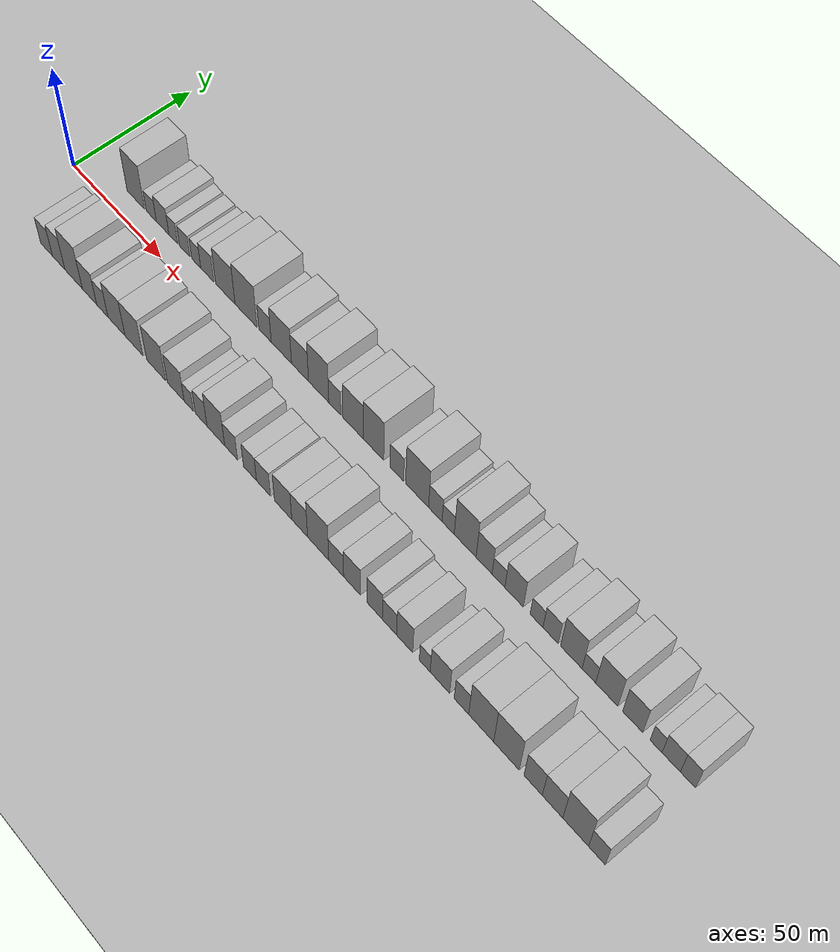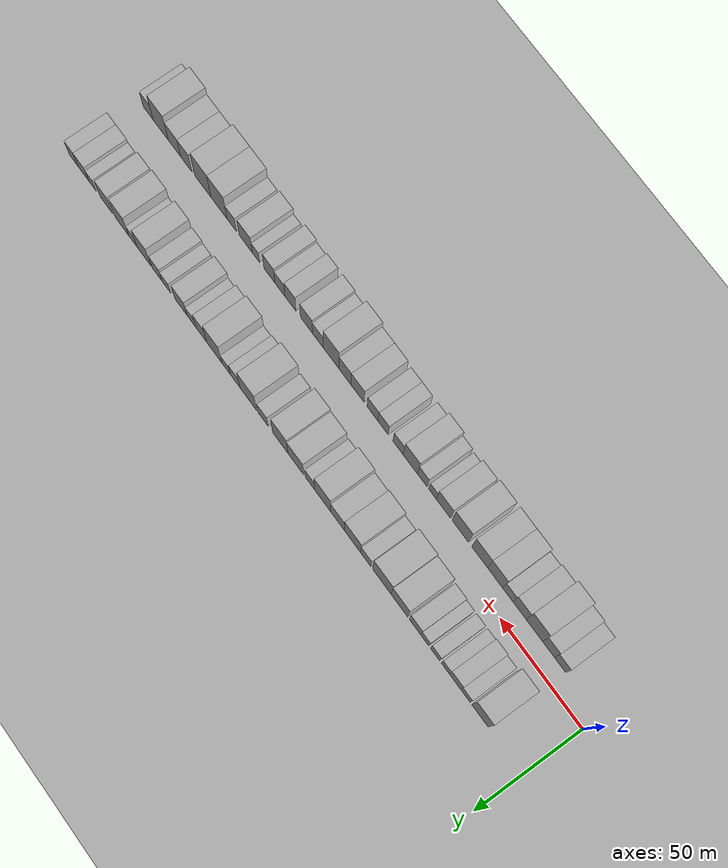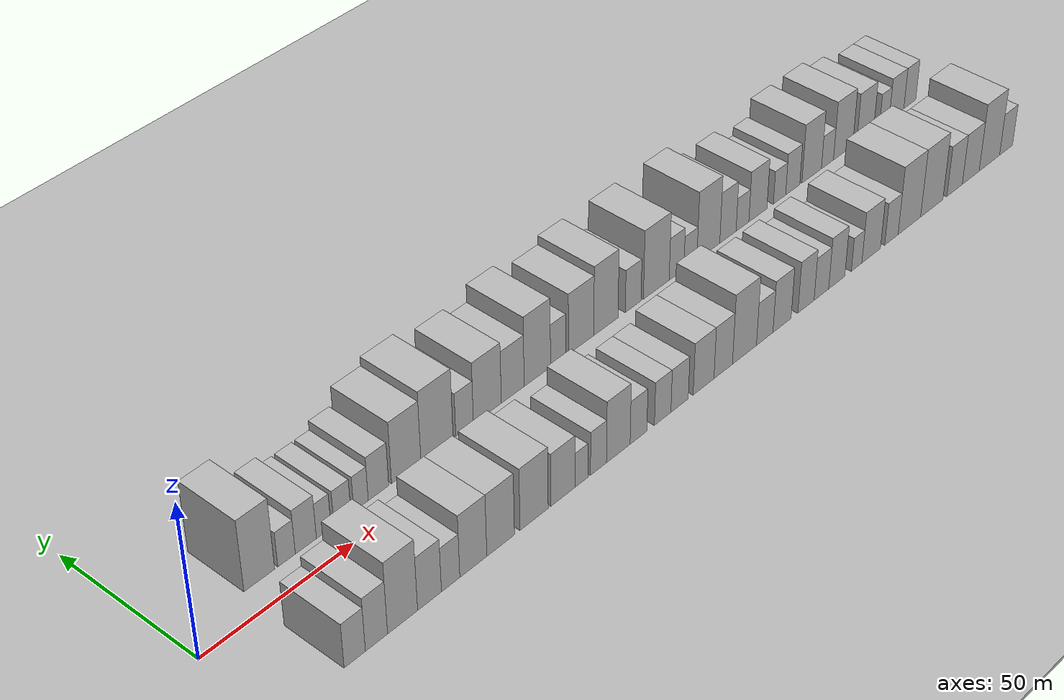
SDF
<?xml version="1.0" encoding="utf-8"?>

<sdf version="1.6">

   <world name="default">

      <gui fullscreen="0">

         <camera name="user_camera">

            <pose>-15 0 4.57585 0 0 0</pose>

            <view_controller>orbit</view_controller>

         </camera>

      </gui>

      <scene>

         <sky>

           <clouds>

             <speed>12</speed>

           </clouds>

         </sky>

         <ambient>0.4 0.4 0.4 1</ambient>

         <background>0.7 0.7 0.7 1</background>

         <shadows>1</shadows>

      </scene>

      <gravity>0 0 -9.8066</gravity>

      <magnetic_field>6e-06 2.3e-05 -4.2e-05</magnetic_field>

      <physics default="0" name="default_physics" type="ode">

         <ode>

            <solver>

               <type>quick</type>

               <iters>10</iters>

               <sor>1.0</sor>

               <use_dynamic_moi_rescaling>0</use_dynamic_moi_rescaling>

            </solver>

            <constraints>

               <cfm>0</cfm>

               <erp>0.2</erp>

               <contact_max_correcting_vel>100</contact_max_correcting_vel>

               <contact_surface_layer>0.001</contact_surface_layer>

            </constraints>

         </ode>

         <max_step_size>0.004</max_step_size>

         <real_time_factor>1</real_time_factor>

         <real_time_update_rate>250</real_time_update_rate>

      </physics>

      <light name="sun" type="directional">

         <cast_shadows>1</cast_shadows>

         <pose>0 0 10 0 0 0</pose>

         <diffuse>0.8 0.8 0.8 1</diffuse>

         <specular>0.2 0.2 0.2 1</specular>

         <attenuation>

            <range>1000</range>

            <constant>0.9</constant>

            <linear>0.01</linear>

            <quadratic>0.001</quadratic>

         </attenuation>

         <direction>-0.5 0.1 -0.9</direction>

      </light>

      <include>

         <name>ground_plane_1</name>

         <uri>model://HANNAS_ground_plane</uri>

         <pose>0 0 0  0 0 0</pose>

      </include>

      <include>

         <name>ground_plane_2</name>

         <uri>model://HANNAS_ground_plane</uri>

         <pose>100 0 0  0 0 0</pose>

      </include>

      <model name="building_1">

         <static>1</static>

         <pose frame="">25.9712 17.5000 0 0.000000 0.000000 1.570796</pose>

         <link name="link">

            <pose frame="">0 0 12.00 0 0 0</pose>

            <collision name="collision">

               <geometry>

                  <box>

                     <size>20.0000 9.9424 24.0000</size>

                  </box>

               </geometry>

               <max_contacts>10</max_contacts>

               <surface>

                  <contact>

                     <ode/>

                  </contact>

                  <bounce/>

                  <friction>

                     <torsional>

                        <ode/>

                     </torsional>

                     <ode/>

                  </friction>

               </surface>

            </collision>

            <visual name="visual">

               <cast_shadows>0</cast_shadows>

               <geometry>

                  <box>

                     <size>20.0000 9.9424 24.0000</size>

                  </box>

               </geometry>

               <material>

                  <script>

                     <uri>model://HANNAS_wall/materials/scripts</uri>

                     <uri>model://HANNAS_wall/materials/textures</uri>

                     <name>vrc/HANNAS_wall</name>

                  </script>

               </material>

            </visual>

            <self_collide>0</self_collide>

            <enable_wind>0</enable_wind>

            <kinematic>0</kinematic>

         </link>

      </model>

      <model name="building_2">

         <static>1</static>

         <pose frame="">34.8163 17.5000 0 0.000000 0.000000 1.570796</pose>

         <link name="link">

            <pose frame="">0 0 6.00 0 0 0</pose>

            <collision name="collision">

               <geometry>

                  <box>

                     <size>20.0000 5.7477 12.0000</size>

                  </box>

               </geometry>

               <max_contacts>10</max_contacts>

               <surface>

                  <contact>

                     <ode/>

                  </contact>

                  <bounce/>

                  <friction>

                     <torsional>

                        <ode/>

                     </torsional>

                     <ode/>

                  </friction>

               </surface>

            </collision>

            <visual name="visual">

               <cast_shadows>0</cast_shadows>

               <geometry>

                  <box>

                     <size>20.0000 5.7477 12.0000</size>

                  </box>

               </geometry>

               <material>

                  <script>

                     <uri>model://HANNAS_wall/materials/scripts</uri>

                     <uri>model://HANNAS_wall/materials/textures</uri>

                     <name>vrc/HANNAS_wall</name>

                  </script>

               </material>

            </visual>

            <self_collide>0</self_collide>

            <enable_wind>0</enable_wind>

            <kinematic>0</kinematic>

         </link>

      </model>

      <model name="building_3">

         <static>1</static>

         <pose frame="">41.1859 17.5000 0 0.000000 0.000000 1.570796</pose>

         <link name="link">

            <pose frame="">0 0 7.50 0 0 0</pose>

            <collision name="collision">

               <geometry>

                  <box>

                     <size>20.0000 6.9916 15.0000</size>

                  </box>

               </geometry>

               <max_contacts>10</max_contacts>

               <surface>

                  <contact>

                     <ode/>

                  </contact>

                  <bounce/>

                  <friction>

                     <torsional>

                        <ode/>

                     </torsional>

                     <ode/>

                  </friction>

               </surface>

            </collision>

            <visual name="visual">

               <cast_shadows>0</cast_shadows>

               <geometry>

                  <box>

                     <size>20.0000 6.9916 15.0000</size>

                  </box>

               </geometry>

               <material>

                  <script>

                     <uri>model://HANNAS_wall/materials/scripts</uri>

                     <uri>model://HANNAS_wall/materials/textures</uri>

                     <name>vrc/HANNAS_wall</name>

                  </script>

               </material>

            </visual>

            <self_collide>0</self_collide>

            <enable_wind>0</enable_wind>

            <kinematic>0</kinematic>

         </link>

      </model>

      <model name="building_4">

         <static>1</static>

         <pose frame="">47.1388 17.5000 0 0.000000 0.000000 1.570796</pose>

         <link name="link">

            <pose frame="">0 0 6.00 0 0 0</pose>

            <collision name="collision">

               <geometry>

                  <box>

                     <size>20.0000 4.9142 12.0000</size>

                  </box>

               </geometry>

               <max_contacts>10</max_contacts>

               <surface>

                  <contact>

                     <ode/>

                  </contact>

                  <bounce/>

                  <friction>

                     <torsional>

                        <ode/>

                     </torsional>

                     <ode/>

                  </friction>

               </surface>

            </collision>

            <visual name="visual">

               <cast_shadows>0</cast_shadows>

               <geometry>

                  <box>

                     <size>20.0000 4.9142 12.0000</size>

                  </box>

               </geometry>

               <material>

                  <script>

                     <uri>model://HANNAS_wall/materials/scripts</uri>

                     <uri>model://HANNAS_wall/materials/textures</uri>

                     <name>vrc/HANNAS_wall</name>

                  </script>

               </material>

            </visual>

            <self_collide>0</self_collide>

            <enable_wind>0</enable_wind>

            <kinematic>0</kinematic>

         </link>

      </model>

      <model name="building_5">

         <static>1</static>

         <pose frame="">53.4631 17.5000 0 0.000000 0.000000 1.570796</pose>

         <link name="link">

            <pose frame="">0 0 6.00 0 0 0</pose>

            <collision name="collision">

               <geometry>

                  <box>

                     <size>20.0000 5.7344 12.0000</size>

                  </box>

               </geometry>

               <max_contacts>10</max_contacts>

               <surface>

                  <contact>

                     <ode/>

                  </contact>

                  <bounce/>

                  <friction>

                     <torsional>

                        <ode/>

                     </torsional>

                     <ode/>

                  </friction>

               </surface>

            </collision>

            <visual name="visual">

               <cast_shadows>0</cast_shadows>

               <geometry>

                  <box>

                     <size>20.0000 5.7344 12.0000</size>

                  </box>

               </geometry>

               <material>

                  <script>

                     <uri>model://HANNAS_wall/materials/scripts</uri>

                     <uri>model://HANNAS_wall/materials/textures</uri>

                     <name>vrc/HANNAS_wall</name>

                  </script>

               </material>

            </visual>

            <self_collide>0</self_collide>

            <enable_wind>0</enable_wind>

            <kinematic>0</kinematic>

         </link>

      </model>

      <model name="building_6">

         <static>1</static>

         <pose frame="">59.8176 17.5000 0 0.000000 0.000000 1.570796</pose>

         <link name="link">

            <pose frame="">0 0 6.00 0 0 0</pose>

            <collision name="collision">

               <geometry>

                  <box>

                     <size>20.0000 4.9748 12.0000</size>

                  </box>

               </geometry>

               <max_contacts>10</max_contacts>

               <surface>

                  <contact>

                     <ode/>

                  </contact>

                  <bounce/>

                  <friction>

                     <torsional>

                        <ode/>

                     </torsional>

                     <ode/>

                  </friction>

               </surface>

            </collision>

            <visual name="visual">

               <cast_shadows>0</cast_shadows>

               <geometry>

                  <box>

                     <size>20.0000 4.9748 12.0000</size>

                  </box>

               </geometry>

               <material>

                  <script>

                     <uri>model://HANNAS_wall/materials/scripts</uri>

                     <uri>model://HANNAS_wall/materials/textures</uri>

                     <name>vrc/HANNAS_wall</name>

                  </script>

               </material>

            </visual>

            <self_collide>0</self_collide>

            <enable_wind>0</enable_wind>

            <kinematic>0</kinematic>

         </link>

      </model>

      <model name="building_7">

         <static>1</static>

         <pose frame="">65.8682 17.5000 0 0.000000 0.000000 1.570796</pose>

         <link name="link">

            <pose frame="">0 0 7.50 0 0 0</pose>

            <collision name="collision">

               <geometry>

                  <box>

                     <size>20.0000 7.1263 15.0000</size>

                  </box>

               </geometry>

               <max_contacts>10</max_contacts>

               <surface>

                  <contact>

                     <ode/>

                  </contact>

                  <bounce/>

                  <friction>

                     <torsional>

                        <ode/>

                     </torsional>

                     <ode/>

                  </friction>

               </surface>

            </collision>

            <visual name="visual">

               <cast_shadows>0</cast_shadows>

               <geometry>

                  <box>

                     <size>20.0000 7.1263 15.0000</size>

                  </box>

               </geometry>

               <material>

                  <script>

                     <uri>model://HANNAS_wall/materials/scripts</uri>

                     <uri>model://HANNAS_wall/materials/textures</uri>

                     <name>vrc/HANNAS_wall</name>

                  </script>

               </material>

            </visual>

            <self_collide>0</self_collide>

            <enable_wind>0</enable_wind>

            <kinematic>0</kinematic>

         </link>

      </model>

      <model name="building_8">

         <static>1</static>

         <pose frame="">75.6446 17.5000 0 0.000000 0.000000 1.570796</pose>

         <link name="link">

            <pose frame="">0 0 10.50 0 0 0</pose>

            <collision name="collision">

               <geometry>

                  <box>

                     <size>20.0000 10.4266 21.0000</size>

                  </box>

               </geometry>

               <max_contacts>10</max_contacts>

               <surface>

                  <contact>

                     <ode/>

                  </contact>

                  <bounce/>

                  <friction>

                     <torsional>

                        <ode/>

                     </torsional>

                     <ode/>

                  </friction>

               </surface>

            </collision>

            <visual name="visual">

               <cast_shadows>0</cast_shadows>

               <geometry>

                  <box>

                     <size>20.0000 10.4266 21.0000</size>

                  </box>

               </geometry>

               <material>

                  <script>

                     <uri>model://HANNAS_wall/materials/scripts</uri>

                     <uri>model://HANNAS_wall/materials/textures</uri>

                     <name>vrc/HANNAS_wall</name>

                  </script>

               </material>

            </visual>

            <self_collide>0</self_collide>

            <enable_wind>0</enable_wind>

            <kinematic>0</kinematic>

         </link>

      </model>

      <model name="building_9">

         <static>1</static>

         <pose frame="">86.6826 17.5000 0 0.000000 0.000000 1.570796</pose>

         <link name="link">

            <pose frame="">0 0 12.00 0 0 0</pose>

            <collision name="collision">

               <geometry>

                  <box>

                     <size>20.0000 11.6493 24.0000</size>

                  </box>

               </geometry>

               <max_contacts>10</max_contacts>

               <surface>

                  <contact>

                     <ode/>

                  </contact>

                  <bounce/>

                  <friction>

                     <torsional>

                        <ode/>

                     </torsional>

                     <ode/>

                  </friction>

               </surface>

            </collision>

            <visual name="visual">

               <cast_shadows>0</cast_shadows>

               <geometry>

                  <box>

                     <size>20.0000 11.6493 24.0000</size>

                  </box>

               </geometry>

               <material>

                  <script>

                     <uri>model://HANNAS_wall/materials/scripts</uri>

                     <uri>model://HANNAS_wall/materials/textures</uri>

                     <name>vrc/HANNAS_wall</name>

                  </script>

               </material>

            </visual>

            <self_collide>0</self_collide>

            <enable_wind>0</enable_wind>

            <kinematic>0</kinematic>

         </link>

      </model>

      <model name="building_10">

         <static>1</static>

         <pose frame="">96.7625 17.5000 0 0.000000 0.000000 1.570796</pose>

         <link name="link">

            <pose frame="">0 0 7.50 0 0 0</pose>

            <collision name="collision">

               <geometry>

                  <box>

                     <size>20.0000 6.5105 15.0000</size>

                  </box>

               </geometry>

               <max_contacts>10</max_contacts>

               <surface>

                  <contact>

                     <ode/>

                  </contact>

                  <bounce/>

                  <friction>

                     <torsional>

                        <ode/>

                     </torsional>

                     <ode/>

                  </friction>

               </surface>

            </collision>

            <visual name="visual">

               <cast_shadows>0</cast_shadows>

               <geometry>

                  <box>

                     <size>20.0000 6.5105 15.0000</size>

                  </box>

               </geometry>

               <material>

                  <script>

                     <uri>model://HANNAS_wall/materials/scripts</uri>

                     <uri>model://HANNAS_wall/materials/textures</uri>

                     <name>vrc/HANNAS_wall</name>

                  </script>

               </material>

            </visual>

            <self_collide>0</self_collide>

            <enable_wind>0</enable_wind>

            <kinematic>0</kinematic>

         </link>

      </model>

      <model name="building_11">

         <static>1</static>

         <pose frame="">105.2571 17.5000 0 0.000000 0.000000 1.570796</pose>

         <link name="link">

            <pose frame="">0 0 10.50 0 0 0</pose>

            <collision name="collision">

               <geometry>

                  <box>

                     <size>20.0000 10.4787 21.0000</size>

                  </box>

               </geometry>

               <max_contacts>10</max_contacts>

               <surface>

                  <contact>

                     <ode/>

                  </contact>

                  <bounce/>

                  <friction>

                     <torsional>

                        <ode/>

                     </torsional>

                     <ode/>

                  </friction>

               </surface>

            </collision>

            <visual name="visual">

               <cast_shadows>0</cast_shadows>

               <geometry>

                  <box>

                     <size>20.0000 10.4787 21.0000</size>

                  </box>

               </geometry>

               <material>

                  <script>

                     <uri>model://HANNAS_wall/materials/scripts</uri>

                     <uri>model://HANNAS_wall/materials/textures</uri>

                     <name>vrc/HANNAS_wall</name>

                  </script>

               </material>

            </visual>

            <self_collide>0</self_collide>

            <enable_wind>0</enable_wind>

            <kinematic>0</kinematic>

         </link>

      </model>

      <model name="building_12">

         <static>1</static>

         <pose frame="">114.8549 17.5000 0 0.000000 0.000000 1.570796</pose>

         <link name="link">

            <pose frame="">0 0 9.00 0 0 0</pose>

            <collision name="collision">

               <geometry>

                  <box>

                     <size>20.0000 8.7168 18.0000</size>

                  </box>

               </geometry>

               <max_contacts>10</max_contacts>

               <surface>

                  <contact>

                     <ode/>

                  </contact>

                  <bounce/>

                  <friction>

                     <torsional>

                        <ode/>

                     </torsional>

                     <ode/>

                  </friction>

               </surface>

            </collision>

            <visual name="visual">

               <cast_shadows>0</cast_shadows>

               <geometry>

                  <box>

                     <size>20.0000 8.7168 18.0000</size>

                  </box>

               </geometry>

               <material>

                  <script>

                     <uri>model://HANNAS_wall/materials/scripts</uri>

                     <uri>model://HANNAS_wall/materials/textures</uri>

                     <name>vrc/HANNAS_wall</name>

                  </script>

               </material>

            </visual>

            <self_collide>0</self_collide>

            <enable_wind>0</enable_wind>

            <kinematic>0</kinematic>

         </link>

      </model>

      <model name="building_13">

         <static>1</static>

         <pose frame="">124.3384 17.5000 0 0.000000 0.000000 1.570796</pose>

         <link name="link">

            <pose frame="">0 0 12.00 0 0 0</pose>

            <collision name="collision">

               <geometry>

                  <box>

                     <size>20.0000 10.2502 24.0000</size>

                  </box>

               </geometry>

               <max_contacts>10</max_contacts>

               <surface>

                  <contact>

                     <ode/>

                  </contact>

                  <bounce/>

                  <friction>

                     <torsional>

                        <ode/>

                     </torsional>

                     <ode/>

                  </friction>

               </surface>

            </collision>

            <visual name="visual">

               <cast_shadows>0</cast_shadows>

               <geometry>

                  <box>

                     <size>20.0000 10.2502 24.0000</size>

                  </box>

               </geometry>

               <material>

                  <script>

                     <uri>model://HANNAS_wall/materials/scripts</uri>

                     <uri>model://HANNAS_wall/materials/textures</uri>

                     <name>vrc/HANNAS_wall</name>

                  </script>

               </material>

            </visual>

            <self_collide>0</self_collide>

            <enable_wind>0</enable_wind>

            <kinematic>0</kinematic>

         </link>

      </model>

      <model name="building_14">

         <static>1</static>

         <pose frame="">132.4854 17.5000 0 0.000000 0.000000 1.570796</pose>

         <link name="link">

            <pose frame="">0 0 7.50 0 0 0</pose>

            <collision name="collision">

               <geometry>

                  <box>

                     <size>20.0000 6.0437 15.0000</size>

                  </box>

               </geometry>

               <max_contacts>10</max_contacts>

               <surface>

                  <contact>

                     <ode/>

                  </contact>

                  <bounce/>

                  <friction>

                     <torsional>

                        <ode/>

                     </torsional>

                     <ode/>

                  </friction>

               </surface>

            </collision>

            <visual name="visual">

               <cast_shadows>0</cast_shadows>

               <geometry>

                  <box>

                     <size>20.0000 6.0437 15.0000</size>

                  </box>

               </geometry>

               <material>

                  <script>

                     <uri>model://HANNAS_wall/materials/scripts</uri>

                     <uri>model://HANNAS_wall/materials/textures</uri>

                     <name>vrc/HANNAS_wall</name>

                  </script>

               </material>

            </visual>

            <self_collide>0</self_collide>

            <enable_wind>0</enable_wind>

            <kinematic>0</kinematic>

         </link>

      </model>

      <model name="building_15">

         <static>1</static>

         <pose frame="">141.6110 17.5000 0 0.000000 0.000000 1.570796</pose>

         <link name="link">

            <pose frame="">0 0 10.50 0 0 0</pose>

            <collision name="collision">

               <geometry>

                  <box>

                     <size>20.0000 10.2076 21.0000</size>

                  </box>

               </geometry>

               <max_contacts>10</max_contacts>

               <surface>

                  <contact>

                     <ode/>

                  </contact>

                  <bounce/>

                  <friction>

                     <torsional>

                        <ode/>

                     </torsional>

                     <ode/>

                  </friction>

               </surface>

            </collision>

            <visual name="visual">

               <cast_shadows>0</cast_shadows>

               <geometry>

                  <box>

                     <size>20.0000 10.2076 21.0000</size>

                  </box>

               </geometry>

               <material>

                  <script>

                     <uri>model://HANNAS_wall/materials/scripts</uri>

                     <uri>model://HANNAS_wall/materials/textures</uri>

                     <name>vrc/HANNAS_wall</name>

                  </script>

               </material>

            </visual>

            <self_collide>0</self_collide>

            <enable_wind>0</enable_wind>

            <kinematic>0</kinematic>

         </link>

      </model>

      <model name="building_16">

         <static>1</static>

         <pose frame="">151.6716 17.5000 0 0.000000 0.000000 1.570796</pose>

         <link name="link">

            <pose frame="">0 0 12.00 0 0 0</pose>

            <collision name="collision">

               <geometry>

                  <box>

                     <size>20.0000 9.9136 24.0000</size>

                  </box>

               </geometry>

               <max_contacts>10</max_contacts>

               <surface>

                  <contact>

                     <ode/>

                  </contact>

                  <bounce/>

                  <friction>

                     <torsional>

                        <ode/>

                     </torsional>

                     <ode/>

                  </friction>

               </surface>

            </collision>

            <visual name="visual">

               <cast_shadows>0</cast_shadows>

               <geometry>

                  <box>

                     <size>20.0000 9.9136 24.0000</size>

                  </box>

               </geometry>

               <material>

                  <script>

                     <uri>model://HANNAS_wall/materials/scripts</uri>

                     <uri>model://HANNAS_wall/materials/textures</uri>

                     <name>vrc/HANNAS_wall</name>

                  </script>

               </material>

            </visual>

            <self_collide>0</self_collide>

            <enable_wind>0</enable_wind>

            <kinematic>0</kinematic>

         </link>

      </model>

      <model name="building_17">

         <static>1</static>

         <pose frame="">162.9030 17.5000 0 0.000000 0.000000 1.570796</pose>

         <link name="link">

            <pose frame="">0 0 7.50 0 0 0</pose>

            <collision name="collision">

               <geometry>

                  <box>

                     <size>20.0000 6.5493 15.0000</size>

                  </box>

               </geometry>

               <max_contacts>10</max_contacts>

               <surface>

                  <contact>

                     <ode/>

                  </contact>

                  <bounce/>

                  <friction>

                     <torsional>

                        <ode/>

                     </torsional>

                     <ode/>

                  </friction>

               </surface>

            </collision>

            <visual name="visual">

               <cast_shadows>0</cast_shadows>

               <geometry>

                  <box>

                     <size>20.0000 6.5493 15.0000</size>

                  </box>

               </geometry>

               <material>

                  <script>

                     <uri>model://HANNAS_wall/materials/scripts</uri>

                     <uri>model://HANNAS_wall/materials/textures</uri>

                     <name>vrc/HANNAS_wall</name>

                  </script>

               </material>

            </visual>

            <self_collide>0</self_collide>

            <enable_wind>0</enable_wind>

            <kinematic>0</kinematic>

         </link>

      </model>

      <model name="building_18">

         <static>1</static>

         <pose frame="">172.6414 17.5000 0 0.000000 0.000000 1.570796</pose>

         <link name="link">

            <pose frame="">0 0 12.00 0 0 0</pose>

            <collision name="collision">

               <geometry>

                  <box>

                     <size>20.0000 10.9275 24.0000</size>

                  </box>

               </geometry>

               <max_contacts>10</max_contacts>

               <surface>

                  <contact>

                     <ode/>

                  </contact>

                  <bounce/>

                  <friction>

                     <torsional>

                        <ode/>

                     </torsional>

                     <ode/>

                  </friction>

               </surface>

            </collision>

            <visual name="visual">

               <cast_shadows>0</cast_shadows>

               <geometry>

                  <box>

                     <size>20.0000 10.9275 24.0000</size>

                  </box>

               </geometry>

               <material>

                  <script>

                     <uri>model://HANNAS_wall/materials/scripts</uri>

                     <uri>model://HANNAS_wall/materials/textures</uri>

                     <name>vrc/HANNAS_wall</name>

                  </script>

               </material>

            </visual>

            <self_collide>0</self_collide>

            <enable_wind>0</enable_wind>

            <kinematic>0</kinematic>

         </link>

      </model>

      <model name="building_19">

         <static>1</static>

         <pose frame="">181.2787 17.5000 0 0.000000 0.000000 1.570796</pose>

         <link name="link">

            <pose frame="">0 0 7.50 0 0 0</pose>

            <collision name="collision">

               <geometry>

                  <box>

                     <size>20.0000 6.3471 15.0000</size>

                  </box>

               </geometry>

               <max_contacts>10</max_contacts>

               <surface>

                  <contact>

                     <ode/>

                  </contact>

                  <bounce/>

                  <friction>

                     <torsional>

                        <ode/>

                     </torsional>

                     <ode/>

                  </friction>

               </surface>

            </collision>

            <visual name="visual">

               <cast_shadows>0</cast_shadows>

               <geometry>

                  <box>

                     <size>20.0000 6.3471 15.0000</size>

                  </box>

               </geometry>

               <material>

                  <script>

                     <uri>model://HANNAS_wall/materials/scripts</uri>

                     <uri>model://HANNAS_wall/materials/textures</uri>

                     <name>vrc/HANNAS_wall</name>

                  </script>

               </material>

            </visual>

            <self_collide>0</self_collide>

            <enable_wind>0</enable_wind>

            <kinematic>0</kinematic>

         </link>

      </model>

      <model name="building_20">

         <static>1</static>

         <pose frame="">187.2736 17.5000 0 0.000000 0.000000 1.570796</pose>

         <link name="link">

            <pose frame="">0 0 6.00 0 0 0</pose>

            <collision name="collision">

               <geometry>

                  <box>

                     <size>20.0000 5.6426 12.0000</size>

                  </box>

               </geometry>

               <max_contacts>10</max_contacts>

               <surface>

                  <contact>

                     <ode/>

                  </contact>

                  <bounce/>

                  <friction>

                     <torsional>

                        <ode/>

                     </torsional>

                     <ode/>

                  </friction>

               </surface>

            </collision>

            <visual name="visual">

               <cast_shadows>0</cast_shadows>

               <geometry>

                  <box>

                     <size>20.0000 5.6426 12.0000</size>

                  </box>

               </geometry>

               <material>

                  <script>

                     <uri>model://HANNAS_wall/materials/scripts</uri>

                     <uri>model://HANNAS_wall/materials/textures</uri>

                     <name>vrc/HANNAS_wall</name>

                  </script>

               </material>

            </visual>

            <self_collide>0</self_collide>

            <enable_wind>0</enable_wind>

            <kinematic>0</kinematic>

         </link>

      </model>

      <model name="building_21">

         <static>1</static>

         <pose frame="">195.1427 17.5000 0 0.000000 0.000000 1.570796</pose>

         <link name="link">

            <pose frame="">0 0 12.00 0 0 0</pose>

            <collision name="collision">

               <geometry>

                  <box>

                     <size>20.0000 10.0957 24.0000</size>

                  </box>

               </geometry>

               <max_contacts>10</max_contacts>

               <surface>

                  <contact>

                     <ode/>

                  </contact>

                  <bounce/>

                  <friction>

                     <torsional>

                        <ode/>

                     </torsional>

                     <ode/>

                  </friction>

               </surface>

            </collision>

            <visual name="visual">

               <cast_shadows>0</cast_shadows>

               <geometry>

                  <box>

                     <size>20.0000 10.0957 24.0000</size>

                  </box>

               </geometry>

               <material>

                  <script>

                     <uri>model://HANNAS_wall/materials/scripts</uri>

                     <uri>model://HANNAS_wall/materials/textures</uri>

                     <name>vrc/HANNAS_wall</name>

                  </script>

               </material>

            </visual>

            <self_collide>0</self_collide>

            <enable_wind>0</enable_wind>

            <kinematic>0</kinematic>

         </link>

      </model>

      <model name="building_22">

         <static>1</static>

         <pose frame="">203.8434 17.5000 0 0.000000 0.000000 1.570796</pose>

         <link name="link">

            <pose frame="">0 0 9.00 0 0 0</pose>

            <collision name="collision">

               <geometry>

                  <box>

                     <size>20.0000 7.3057 18.0000</size>

                  </box>

               </geometry>

               <max_contacts>10</max_contacts>

               <surface>

                  <contact>

                     <ode/>

                  </contact>

                  <bounce/>

                  <friction>

                     <torsional>

                        <ode/>

                     </torsional>

                     <ode/>

                  </friction>

               </surface>

            </collision>

            <visual name="visual">

               <cast_shadows>0</cast_shadows>

               <geometry>

                  <box>

                     <size>20.0000 7.3057 18.0000</size>

                  </box>

               </geometry>

               <material>

                  <script>

                     <uri>model://HANNAS_wall/materials/scripts</uri>

                     <uri>model://HANNAS_wall/materials/textures</uri>

                     <name>vrc/HANNAS_wall</name>

                  </script>

               </material>

            </visual>

            <self_collide>0</self_collide>

            <enable_wind>0</enable_wind>

            <kinematic>0</kinematic>

         </link>

      </model>

      <model name="building_23">

         <static>1</static>

         <pose frame="">210.3932 17.5000 0 0.000000 0.000000 1.570796</pose>

         <link name="link">

            <pose frame="">0 0 6.00 0 0 0</pose>

            <collision name="collision">

               <geometry>

                  <box>

                     <size>20.0000 5.7938 12.0000</size>

                  </box>

               </geometry>

               <max_contacts>10</max_contacts>

               <surface>

                  <contact>

                     <ode/>

                  </contact>

                  <bounce/>

                  <friction>

                     <torsional>

                        <ode/>

                     </torsional>

                     <ode/>

                  </friction>

               </surface>

            </collision>

            <visual name="visual">

               <cast_shadows>0</cast_shadows>

               <geometry>

                  <box>

                     <size>20.0000 5.7938 12.0000</size>

                  </box>

               </geometry>

               <material>

                  <script>

                     <uri>model://HANNAS_wall/materials/scripts</uri>

                     <uri>model://HANNAS_wall/materials/textures</uri>

                     <name>vrc/HANNAS_wall</name>

                  </script>

               </material>

            </visual>

            <self_collide>0</self_collide>

            <enable_wind>0</enable_wind>

            <kinematic>0</kinematic>

         </link>

      </model>

      <model name="building_24">

         <static>1</static>

         <pose frame="">217.4280 17.5000 0 0.000000 0.000000 1.570796</pose>

         <link name="link">

            <pose frame="">0 0 9.00 0 0 0</pose>

            <collision name="collision">

               <geometry>

                  <box>

                     <size>20.0000 8.2758 18.0000</size>

                  </box>

               </geometry>

               <max_contacts>10</max_contacts>

               <surface>

                  <contact>

                     <ode/>

                  </contact>

                  <bounce/>

                  <friction>

                     <torsional>

                        <ode/>

                     </torsional>

                     <ode/>

                  </friction>

               </surface>

            </collision>

            <visual name="visual">

               <cast_shadows>0</cast_shadows>

               <geometry>

                  <box>

                     <size>20.0000 8.2758 18.0000</size>

                  </box>

               </geometry>

               <material>

                  <script>

                     <uri>model://HANNAS_wall/materials/scripts</uri>

                     <uri>model://HANNAS_wall/materials/textures</uri>

                     <name>vrc/HANNAS_wall</name>

                  </script>

               </material>

            </visual>

            <self_collide>0</self_collide>

            <enable_wind>0</enable_wind>

            <kinematic>0</kinematic>

         </link>

      </model>

      <model name="building_25">

         <static>1</static>

         <pose frame="">227.4150 17.5000 0 0.000000 0.000000 1.570796</pose>

         <link name="link">

            <pose frame="">0 0 6.00 0 0 0</pose>

            <collision name="collision">

               <geometry>

                  <box>

                     <size>20.0000 5.6981 12.0000</size>

                  </box>

               </geometry>

               <max_contacts>10</max_contacts>

               <surface>

                  <contact>

                     <ode/>

                  </contact>

                  <bounce/>

                  <friction>

                     <torsional>

                        <ode/>

                     </torsional>

                     <ode/>

                  </friction>

               </surface>

            </collision>

            <visual name="visual">

               <cast_shadows>0</cast_shadows>

               <geometry>

                  <box>

                     <size>20.0000 5.6981 12.0000</size>

                  </box>

               </geometry>

               <material>

                  <script>

                     <uri>model://HANNAS_wall/materials/scripts</uri>

                     <uri>model://HANNAS_wall/materials/textures</uri>

                     <name>vrc/HANNAS_wall</name>

                  </script>

               </material>

            </visual>

            <self_collide>0</self_collide>

            <enable_wind>0</enable_wind>

            <kinematic>0</kinematic>

         </link>

      </model>

      <model name="building_26">

         <static>1</static>

         <pose frame="">233.5926 17.5000 0 0.000000 0.000000 1.570796</pose>

         <link name="link">

            <pose frame="">0 0 7.50 0 0 0</pose>

            <collision name="collision">

               <geometry>

                  <box>

                     <size>20.0000 6.6571 15.0000</size>

                  </box>

               </geometry>

               <max_contacts>10</max_contacts>

               <surface>

                  <contact>

                     <ode/>

                  </contact>

                  <bounce/>

                  <friction>

                     <torsional>

                        <ode/>

                     </torsional>

                     <ode/>

                  </friction>

               </surface>

            </collision>

            <visual name="visual">

               <cast_shadows>0</cast_shadows>

               <geometry>

                  <box>

                     <size>20.0000 6.6571 15.0000</size>

                  </box>

               </geometry>

               <material>

                  <script>

                     <uri>model://HANNAS_wall/materials/scripts</uri>

                     <uri>model://HANNAS_wall/materials/textures</uri>

                     <name>vrc/HANNAS_wall</name>

                  </script>

               </material>

            </visual>

            <self_collide>0</self_collide>

            <enable_wind>0</enable_wind>

            <kinematic>0</kinematic>

         </link>

      </model>

      <model name="building_27">

         <static>1</static>

         <pose frame="">242.5889 17.5000 0 0.000000 0.000000 1.570796</pose>

         <link name="link">

            <pose frame="">0 0 10.50 0 0 0</pose>

            <collision name="collision">

               <geometry>

                  <box>

                     <size>20.0000 9.3354 21.0000</size>

                  </box>

               </geometry>

               <max_contacts>10</max_contacts>

               <surface>

                  <contact>

                     <ode/>

                  </contact>

                  <bounce/>

                  <friction>

                     <torsional>

                        <ode/>

                     </torsional>

                     <ode/>

                  </friction>

               </surface>

            </collision>

            <visual name="visual">

               <cast_shadows>0</cast_shadows>

               <geometry>

                  <box>

                     <size>20.0000 9.3354 21.0000</size>

                  </box>

               </geometry>

               <material>

                  <script>

                     <uri>model://HANNAS_wall/materials/scripts</uri>

                     <uri>model://HANNAS_wall/materials/textures</uri>

                     <name>vrc/HANNAS_wall</name>

                  </script>

               </material>

            </visual>

            <self_collide>0</self_collide>

            <enable_wind>0</enable_wind>

            <kinematic>0</kinematic>

         </link>

      </model>

      <model name="building_28">

         <static>1</static>

         <pose frame="">250.1770 17.5000 0 0.000000 0.000000 1.570796</pose>

         <link name="link">

            <pose frame="">0 0 6.00 0 0 0</pose>

            <collision name="collision">

               <geometry>

                  <box>

                     <size>20.0000 5.8409 12.0000</size>

                  </box>

               </geometry>

               <max_contacts>10</max_contacts>

               <surface>

                  <contact>

                     <ode/>

                  </contact>

                  <bounce/>

                  <friction>

                     <torsional>

                        <ode/>

                     </torsional>

                     <ode/>

                  </friction>

               </surface>

            </collision>

            <visual name="visual">

               <cast_shadows>0</cast_shadows>

               <geometry>

                  <box>

                     <size>20.0000 5.8409 12.0000</size>

                  </box>

               </geometry>

               <material>

                  <script>

                     <uri>model://HANNAS_wall/materials/scripts</uri>

                     <uri>model://HANNAS_wall/materials/textures</uri>

                     <name>vrc/HANNAS_wall</name>

                  </script>

               </material>

            </visual>

            <self_collide>0</self_collide>

            <enable_wind>0</enable_wind>

            <kinematic>0</kinematic>

         </link>

      </model>

      <model name="building_29">

         <static>1</static>

         <pose frame="">257.8004 17.5000 0 0.000000 0.000000 1.570796</pose>

         <link name="link">

            <pose frame="">0 0 10.50 0 0 0</pose>

            <collision name="collision">

               <geometry>

                  <box>

                     <size>20.0000 9.4058 21.0000</size>

                  </box>

               </geometry>

               <max_contacts>10</max_contacts>

               <surface>

                  <contact>

                     <ode/>

                  </contact>

                  <bounce/>

                  <friction>

                     <torsional>

                        <ode/>

                     </torsional>

                     <ode/>

                  </friction>

               </surface>

            </collision>

            <visual name="visual">

               <cast_shadows>0</cast_shadows>

               <geometry>

                  <box>

                     <size>20.0000 9.4058 21.0000</size>

                  </box>

               </geometry>

               <material>

                  <script>

                     <uri>model://HANNAS_wall/materials/scripts</uri>

                     <uri>model://HANNAS_wall/materials/textures</uri>

                     <name>vrc/HANNAS_wall</name>

                  </script>

               </material>

            </visual>

            <self_collide>0</self_collide>

            <enable_wind>0</enable_wind>

            <kinematic>0</kinematic>

         </link>

      </model>

      <model name="building_30">

         <static>1</static>

         <pose frame="">268.7060 17.5000 0 0.000000 0.000000 1.570796</pose>

         <link name="link">

            <pose frame="">0 0 9.00 0 0 0</pose>

            <collision name="collision">

               <geometry>

                  <box>

                     <size>20.0000 8.4054 18.0000</size>

                  </box>

               </geometry>

               <max_contacts>10</max_contacts>

               <surface>

                  <contact>

                     <ode/>

                  </contact>

                  <bounce/>

                  <friction>

                     <torsional>

                        <ode/>

                     </torsional>

                     <ode/>

                  </friction>

               </surface>

            </collision>

            <visual name="visual">

               <cast_shadows>0</cast_shadows>

               <geometry>

                  <box>

                     <size>20.0000 8.4054 18.0000</size>

                  </box>

               </geometry>

               <material>

                  <script>

                     <uri>model://HANNAS_wall/materials/scripts</uri>

                     <uri>model://HANNAS_wall/materials/textures</uri>

                     <name>vrc/HANNAS_wall</name>

                  </script>

               </material>

            </visual>

            <self_collide>0</self_collide>

            <enable_wind>0</enable_wind>

            <kinematic>0</kinematic>

         </link>

      </model>

      <model name="building_31">

         <static>1</static>

         <pose frame="">278.3729 17.5000 0 0.000000 0.000000 1.570796</pose>

         <link name="link">

            <pose frame="">0 0 6.00 0 0 0</pose>

            <collision name="collision">

               <geometry>

                  <box>

                     <size>20.0000 4.9284 12.0000</size>

                  </box>

               </geometry>

               <max_contacts>10</max_contacts>

               <surface>

                  <contact>

                     <ode/>

                  </contact>

                  <bounce/>

                  <friction>

                     <torsional>

                        <ode/>

                     </torsional>

                     <ode/>

                  </friction>

               </surface>

            </collision>

            <visual name="visual">

               <cast_shadows>0</cast_shadows>

               <geometry>

                  <box>

                     <size>20.0000 4.9284 12.0000</size>

                  </box>

               </geometry>

               <material>

                  <script>

                     <uri>model://HANNAS_wall/materials/scripts</uri>

                     <uri>model://HANNAS_wall/materials/textures</uri>

                     <name>vrc/HANNAS_wall</name>

                  </script>

               </material>

            </visual>

            <self_collide>0</self_collide>

            <enable_wind>0</enable_wind>

            <kinematic>0</kinematic>

         </link>

      </model>

      <model name="building_32">

         <static>1</static>

         <pose frame="">284.5853 17.5000 0 0.000000 0.000000 1.570796</pose>

         <link name="link">

            <pose frame="">0 0 7.50 0 0 0</pose>

            <collision name="collision">

               <geometry>

                  <box>

                     <size>20.0000 7.4963 15.0000</size>

                  </box>

               </geometry>

               <max_contacts>10</max_contacts>

               <surface>

                  <contact>

                     <ode/>

                  </contact>

                  <bounce/>

                  <friction>

                     <torsional>

                        <ode/>

                     </torsional>

                     <ode/>

                  </friction>

               </surface>

            </collision>

            <visual name="visual">

               <cast_shadows>0</cast_shadows>

               <geometry>

                  <box>

                     <size>20.0000 7.4963 15.0000</size>

                  </box>

               </geometry>

               <material>

                  <script>

                     <uri>model://HANNAS_wall/materials/scripts</uri>

                     <uri>model://HANNAS_wall/materials/textures</uri>

                     <name>vrc/HANNAS_wall</name>

                  </script>

               </material>

            </visual>

            <self_collide>0</self_collide>

            <enable_wind>0</enable_wind>

            <kinematic>0</kinematic>

         </link>

      </model>

      <model name="building_33">

         <static>1</static>

         <pose frame="">291.4075 17.5000 0 0.000000 0.000000 1.570796</pose>

         <link name="link">

            <pose frame="">0 0 7.50 0 0 0</pose>

            <collision name="collision">

               <geometry>

                  <box>

                     <size>20.0000 6.1482 15.0000</size>

                  </box>

               </geometry>

               <max_contacts>10</max_contacts>

               <surface>

                  <contact>

                     <ode/>

                  </contact>

                  <bounce/>

                  <friction>

                     <torsional>

                        <ode/>

                     </torsional>

                     <ode/>

                  </friction>

               </surface>

            </collision>

            <visual name="visual">

               <cast_shadows>0</cast_shadows>

               <geometry>

                  <box>

                     <size>20.0000 6.1482 15.0000</size>

                  </box>

               </geometry>

               <material>

                  <script>

                     <uri>model://HANNAS_wall/materials/scripts</uri>

                     <uri>model://HANNAS_wall/materials/textures</uri>

                     <name>vrc/HANNAS_wall</name>

                  </script>

               </material>

            </visual>

            <self_collide>0</self_collide>

            <enable_wind>0</enable_wind>

            <kinematic>0</kinematic>

         </link>

      </model>

      <model name="building_34">

         <static>1</static>

         <pose frame="">23.4213 -17.5000 0 0.000000 0.000000 1.570796</pose>

         <link name="link">

            <pose frame="">0 0 7.50 0 0 0</pose>

            <collision name="collision">

               <geometry>

                  <box>

                     <size>20.0000 6.8426 15.0000</size>

                  </box>

               </geometry>

               <max_contacts>10</max_contacts>

               <surface>

                  <contact>

                     <ode/>

                  </contact>

                  <bounce/>

                  <friction>

                     <torsional>

                        <ode/>

                     </torsional>

                     <ode/>

                  </friction>

               </surface>

            </collision>

            <visual name="visual">

               <cast_shadows>0</cast_shadows>

               <geometry>

                  <box>

                     <size>20.0000 6.8426 15.0000</size>

                  </box>

               </geometry>

               <material>

                  <script>

                     <uri>model://HANNAS_wall/materials/scripts</uri>

                     <uri>model://HANNAS_wall/materials/textures</uri>

                     <name>vrc/HANNAS_wall</name>

                  </script>

               </material>

            </visual>

            <self_collide>0</self_collide>

            <enable_wind>0</enable_wind>

            <kinematic>0</kinematic>

         </link>

      </model>

      <model name="building_35">

         <static>1</static>

         <pose frame="">30.4554 -17.5000 0 0.000000 0.000000 1.570796</pose>

         <link name="link">

            <pose frame="">0 0 9.00 0 0 0</pose>

            <collision name="collision">

               <geometry>

                  <box>

                     <size>20.0000 7.2256 18.0000</size>

                  </box>

               </geometry>

               <max_contacts>10</max_contacts>

               <surface>

                  <contact>

                     <ode/>

                  </contact>

                  <bounce/>

                  <friction>

                     <torsional>

                        <ode/>

                     </torsional>

                     <ode/>

                  </friction>

               </surface>

            </collision>

            <visual name="visual">

               <cast_shadows>0</cast_shadows>

               <geometry>

                  <box>

                     <size>20.0000 7.2256 18.0000</size>

                  </box>

               </geometry>

               <material>

                  <script>

                     <uri>model://HANNAS_wall/materials/scripts</uri>

                     <uri>model://HANNAS_wall/materials/textures</uri>

                     <name>vrc/HANNAS_wall</name>

                  </script>

               </material>

            </visual>

            <self_collide>0</self_collide>

            <enable_wind>0</enable_wind>

            <kinematic>0</kinematic>

         </link>

      </model>

      <model name="building_36">

         <static>1</static>

         <pose frame="">39.0456 -17.5000 0 0.000000 0.000000 1.570796</pose>

         <link name="link">

            <pose frame="">0 0 12.00 0 0 0</pose>

            <collision name="collision">

               <geometry>

                  <box>

                     <size>20.0000 9.9546 24.0000</size>

                  </box>

               </geometry>

               <max_contacts>10</max_contacts>

               <surface>

                  <contact>

                     <ode/>

                  </contact>

                  <bounce/>

                  <friction>

                     <torsional>

                        <ode/>

                     </torsional>

                     <ode/>

                  </friction>

               </surface>

            </collision>

            <visual name="visual">

               <cast_shadows>0</cast_shadows>

               <geometry>

                  <box>

                     <size>20.0000 9.9546 24.0000</size>

                  </box>

               </geometry>

               <material>

                  <script>

                     <uri>model://HANNAS_wall/materials/scripts</uri>

                     <uri>model://HANNAS_wall/materials/textures</uri>

                     <name>vrc/HANNAS_wall</name>

                  </script>

               </material>

            </visual>

            <self_collide>0</self_collide>

            <enable_wind>0</enable_wind>

            <kinematic>0</kinematic>

         </link>

      </model>

      <model name="building_37">

         <static>1</static>

         <pose frame="">48.0457 -17.5000 0 0.000000 0.000000 1.570796</pose>

         <link name="link">

            <pose frame="">0 0 9.00 0 0 0</pose>

            <collision name="collision">

               <geometry>

                  <box>

                     <size>20.0000 8.0457 18.0000</size>

                  </box>

               </geometry>

               <max_contacts>10</max_contacts>

               <surface>

                  <contact>

                     <ode/>

                  </contact>

                  <bounce/>

                  <friction>

                     <torsional>

                        <ode/>

                     </torsional>

                     <ode/>

                  </friction>

               </surface>

            </collision>

            <visual name="visual">

               <cast_shadows>0</cast_shadows>

               <geometry>

                  <box>

                     <size>20.0000 8.0457 18.0000</size>

                  </box>

               </geometry>

               <material>

                  <script>

                     <uri>model://HANNAS_wall/materials/scripts</uri>

                     <uri>model://HANNAS_wall/materials/textures</uri>

                     <name>vrc/HANNAS_wall</name>

                  </script>

               </material>

            </visual>

            <self_collide>0</self_collide>

            <enable_wind>0</enable_wind>

            <kinematic>0</kinematic>

         </link>

      </model>

      <model name="building_38">

         <static>1</static>

         <pose frame="">55.2150 -17.5000 0 0.000000 0.000000 1.570796</pose>

         <link name="link">

            <pose frame="">0 0 7.50 0 0 0</pose>

            <collision name="collision">

               <geometry>

                  <box>

                     <size>20.0000 6.2928 15.0000</size>

                  </box>

               </geometry>

               <max_contacts>10</max_contacts>

               <surface>

                  <contact>

                     <ode/>

                  </contact>

                  <bounce/>

                  <friction>

                     <torsional>

                        <ode/>

                     </torsional>

                     <ode/>

                  </friction>

               </surface>

            </collision>

            <visual name="visual">

               <cast_shadows>0</cast_shadows>

               <geometry>

                  <box>

                     <size>20.0000 6.2928 15.0000</size>

                  </box>

               </geometry>

               <material>

                  <script>

                     <uri>model://HANNAS_wall/materials/scripts</uri>

                     <uri>model://HANNAS_wall/materials/textures</uri>

                     <name>vrc/HANNAS_wall</name>

                  </script>

               </material>

            </visual>

            <self_collide>0</self_collide>

            <enable_wind>0</enable_wind>

            <kinematic>0</kinematic>

         </link>

      </model>

      <model name="building_39">

         <static>1</static>

         <pose frame="">63.0596 -17.5000 0 0.000000 0.000000 1.570796</pose>

         <link name="link">

            <pose frame="">0 0 10.50 0 0 0</pose>

            <collision name="collision">

               <geometry>

                  <box>

                     <size>20.0000 9.3964 21.0000</size>

                  </box>

               </geometry>

               <max_contacts>10</max_contacts>

               <surface>

                  <contact>

                     <ode/>

                  </contact>

                  <bounce/>

                  <friction>

                     <torsional>

                        <ode/>

                     </torsional>

                     <ode/>

                  </friction>

               </surface>

            </collision>

            <visual name="visual">

               <cast_shadows>0</cast_shadows>

               <geometry>

                  <box>

                     <size>20.0000 9.3964 21.0000</size>

                  </box>

               </geometry>

               <material>

                  <script>

                     <uri>model://HANNAS_wall/materials/scripts</uri>

                     <uri>model://HANNAS_wall/materials/textures</uri>

                     <name>vrc/HANNAS_wall</name>

                  </script>

               </material>

            </visual>

            <self_collide>0</self_collide>

            <enable_wind>0</enable_wind>

            <kinematic>0</kinematic>

         </link>

      </model>

      <model name="building_40">

         <static>1</static>

         <pose frame="">72.6556 -17.5000 0 0.000000 0.000000 1.570796</pose>

         <link name="link">

            <pose frame="">0 0 10.50 0 0 0</pose>

            <collision name="collision">

               <geometry>

                  <box>

                     <size>20.0000 9.7955 21.0000</size>

                  </box>

               </geometry>

               <max_contacts>10</max_contacts>

               <surface>

                  <contact>

                     <ode/>

                  </contact>

                  <bounce/>

                  <friction>

                     <torsional>

                        <ode/>

                     </torsional>

                     <ode/>

                  </friction>

               </surface>

            </collision>

            <visual name="visual">

               <cast_shadows>0</cast_shadows>

               <geometry>

                  <box>

                     <size>20.0000 9.7955 21.0000</size>

                  </box>

               </geometry>

               <material>

                  <script>

                     <uri>model://HANNAS_wall/materials/scripts</uri>

                     <uri>model://HANNAS_wall/materials/textures</uri>

                     <name>vrc/HANNAS_wall</name>

                  </script>

               </material>

            </visual>

            <self_collide>0</self_collide>

            <enable_wind>0</enable_wind>

            <kinematic>0</kinematic>

         </link>

      </model>

      <model name="building_41">

         <static>1</static>

         <pose frame="">84.6674 -17.5000 0 0.000000 0.000000 1.570796</pose>

         <link name="link">

            <pose frame="">0 0 10.50 0 0 0</pose>

            <collision name="collision">

               <geometry>

                  <box>

                     <size>20.0000 10.2282 21.0000</size>

                  </box>

               </geometry>

               <max_contacts>10</max_contacts>

               <surface>

                  <contact>

                     <ode/>

                  </contact>

                  <bounce/>

                  <friction>

                     <torsional>

                        <ode/>

                     </torsional>

                     <ode/>

                  </friction>

               </surface>

            </collision>

            <visual name="visual">

               <cast_shadows>0</cast_shadows>

               <geometry>

                  <box>

                     <size>20.0000 10.2282 21.0000</size>

                  </box>

               </geometry>

               <material>

                  <script>

                     <uri>model://HANNAS_wall/materials/scripts</uri>

                     <uri>model://HANNAS_wall/materials/textures</uri>

                     <name>vrc/HANNAS_wall</name>

                  </script>

               </material>

            </visual>

            <self_collide>0</self_collide>

            <enable_wind>0</enable_wind>

            <kinematic>0</kinematic>

         </link>

      </model>

      <model name="building_42">

         <static>1</static>

         <pose frame="">95.2177 -17.5000 0 0.000000 0.000000 1.570796</pose>

         <link name="link">

            <pose frame="">0 0 9.00 0 0 0</pose>

            <collision name="collision">

               <geometry>

                  <box>

                     <size>20.0000 8.8724 18.0000</size>

                  </box>

               </geometry>

               <max_contacts>10</max_contacts>

               <surface>

                  <contact>

                     <ode/>

                  </contact>

                  <bounce/>

                  <friction>

                     <torsional>

                        <ode/>

                     </torsional>

                     <ode/>

                  </friction>

               </surface>

            </collision>

            <visual name="visual">

               <cast_shadows>0</cast_shadows>

               <geometry>

                  <box>

                     <size>20.0000 8.8724 18.0000</size>

                  </box>

               </geometry>

               <material>

                  <script>

                     <uri>model://HANNAS_wall/materials/scripts</uri>

                     <uri>model://HANNAS_wall/materials/textures</uri>

                     <name>vrc/HANNAS_wall</name>

                  </script>

               </material>

            </visual>

            <self_collide>0</self_collide>

            <enable_wind>0</enable_wind>

            <kinematic>0</kinematic>

         </link>

      </model>

      <model name="building_43">

         <static>1</static>

         <pose frame="">102.0926 -17.5000 0 0.000000 0.000000 1.570796</pose>

         <link name="link">

            <pose frame="">0 0 6.00 0 0 0</pose>

            <collision name="collision">

               <geometry>

                  <box>

                     <size>20.0000 4.8774 12.0000</size>

                  </box>

               </geometry>

               <max_contacts>10</max_contacts>

               <surface>

                  <contact>

                     <ode/>

                  </contact>

                  <bounce/>

                  <friction>

                     <torsional>

                        <ode/>

                     </torsional>

                     <ode/>

                  </friction>

               </surface>

            </collision>

            <visual name="visual">

               <cast_shadows>0</cast_shadows>

               <geometry>

                  <box>

                     <size>20.0000 4.8774 12.0000</size>

                  </box>

               </geometry>

               <material>

                  <script>

                     <uri>model://HANNAS_wall/materials/scripts</uri>

                     <uri>model://HANNAS_wall/materials/textures</uri>

                     <name>vrc/HANNAS_wall</name>

                  </script>

               </material>

            </visual>

            <self_collide>0</self_collide>

            <enable_wind>0</enable_wind>

            <kinematic>0</kinematic>

         </link>

      </model>

      <model name="building_44">

         <static>1</static>

         <pose frame="">108.5644 -17.5000 0 0.000000 0.000000 1.570796</pose>

         <link name="link">

            <pose frame="">0 0 7.50 0 0 0</pose>

            <collision name="collision">

               <geometry>

                  <box>

                     <size>20.0000 6.0662 15.0000</size>

                  </box>

               </geometry>

               <max_contacts>10</max_contacts>

               <surface>

                  <contact>

                     <ode/>

                  </contact>

                  <bounce/>

                  <friction>

                     <torsional>

                        <ode/>

                     </torsional>

                     <ode/>

                  </friction>

               </surface>

            </collision>

            <visual name="visual">

               <cast_shadows>0</cast_shadows>

               <geometry>

                  <box>

                     <size>20.0000 6.0662 15.0000</size>

                  </box>

               </geometry>

               <material>

                  <script>

                     <uri>model://HANNAS_wall/materials/scripts</uri>

                     <uri>model://HANNAS_wall/materials/textures</uri>

                     <name>vrc/HANNAS_wall</name>

                  </script>

               </material>

            </visual>

            <self_collide>0</self_collide>

            <enable_wind>0</enable_wind>

            <kinematic>0</kinematic>

         </link>

      </model>

      <model name="building_45">

         <static>1</static>

         <pose frame="">116.1612 -17.5000 0 0.000000 0.000000 1.570796</pose>

         <link name="link">

            <pose frame="">0 0 10.50 0 0 0</pose>

            <collision name="collision">

               <geometry>

                  <box>

                     <size>20.0000 9.1274 21.0000</size>

                  </box>

               </geometry>

               <max_contacts>10</max_contacts>

               <surface>

                  <contact>

                     <ode/>

                  </contact>

                  <bounce/>

                  <friction>

                     <torsional>

                        <ode/>

                     </torsional>

                     <ode/>

                  </friction>

               </surface>

            </collision>

            <visual name="visual">

               <cast_shadows>0</cast_shadows>

               <geometry>

                  <box>

                     <size>20.0000 9.1274 21.0000</size>

                  </box>

               </geometry>

               <material>

                  <script>

                     <uri>model://HANNAS_wall/materials/scripts</uri>

                     <uri>model://HANNAS_wall/materials/textures</uri>

                     <name>vrc/HANNAS_wall</name>

                  </script>

               </material>

            </visual>

            <self_collide>0</self_collide>

            <enable_wind>0</enable_wind>

            <kinematic>0</kinematic>

         </link>

      </model>

      <model name="building_46">

         <static>1</static>

         <pose frame="">124.0080 -17.5000 0 0.000000 0.000000 1.570796</pose>

         <link name="link">

            <pose frame="">0 0 7.50 0 0 0</pose>

            <collision name="collision">

               <geometry>

                  <box>

                     <size>20.0000 6.5663 15.0000</size>

                  </box>

               </geometry>

               <max_contacts>10</max_contacts>

               <surface>

                  <contact>

                     <ode/>

                  </contact>

                  <bounce/>

                  <friction>

                     <torsional>

                        <ode/>

                     </torsional>

                     <ode/>

                  </friction>

               </surface>

            </collision>

            <visual name="visual">

               <cast_shadows>0</cast_shadows>

               <geometry>

                  <box>

                     <size>20.0000 6.5663 15.0000</size>

                  </box>

               </geometry>

               <material>

                  <script>

                     <uri>model://HANNAS_wall/materials/scripts</uri>

                     <uri>model://HANNAS_wall/materials/textures</uri>

                     <name>vrc/HANNAS_wall</name>

                  </script>

               </material>

            </visual>

            <self_collide>0</self_collide>

            <enable_wind>0</enable_wind>

            <kinematic>0</kinematic>

         </link>

      </model>

      <model name="building_47">

         <static>1</static>

         <pose frame="">133.5781 -17.5000 0 0.000000 0.000000 1.570796</pose>

         <link name="link">

            <pose frame="">0 0 7.50 0 0 0</pose>

            <collision name="collision">

               <geometry>

                  <box>

                     <size>20.0000 6.5737 15.0000</size>

                  </box>

               </geometry>

               <max_contacts>10</max_contacts>

               <surface>

                  <contact>

                     <ode/>

                  </contact>

                  <bounce/>

                  <friction>

                     <torsional>

                        <ode/>

                     </torsional>

                     <ode/>

                  </friction>

               </surface>

            </collision>

            <visual name="visual">

               <cast_shadows>0</cast_shadows>

               <geometry>

                  <box>

                     <size>20.0000 6.5737 15.0000</size>

                  </box>

               </geometry>

               <material>

                  <script>

                     <uri>model://HANNAS_wall/materials/scripts</uri>

                     <uri>model://HANNAS_wall/materials/textures</uri>

                     <name>vrc/HANNAS_wall</name>

                  </script>

               </material>

            </visual>

            <self_collide>0</self_collide>

            <enable_wind>0</enable_wind>

            <kinematic>0</kinematic>

         </link>

      </model>

      <model name="building_48">

         <static>1</static>

         <pose frame="">140.3663 -17.5000 0 0.000000 0.000000 1.570796</pose>

         <link name="link">

            <pose frame="">0 0 7.50 0 0 0</pose>

            <collision name="collision">

               <geometry>

                  <box>

                     <size>20.0000 7.0029 15.0000</size>

                  </box>

               </geometry>

               <max_contacts>10</max_contacts>

               <surface>

                  <contact>

                     <ode/>

                  </contact>

                  <bounce/>

                  <friction>

                     <torsional>

                        <ode/>

                     </torsional>

                     <ode/>

                  </friction>

               </surface>

            </collision>

            <visual name="visual">

               <cast_shadows>0</cast_shadows>

               <geometry>

                  <box>

                     <size>20.0000 7.0029 15.0000</size>

                  </box>

               </geometry>

               <material>

                  <script>

                     <uri>model://HANNAS_wall/materials/scripts</uri>

                     <uri>model://HANNAS_wall/materials/textures</uri>

                     <name>vrc/HANNAS_wall</name>

                  </script>

               </material>

            </visual>

            <self_collide>0</self_collide>

            <enable_wind>0</enable_wind>

            <kinematic>0</kinematic>

         </link>

      </model>

      <model name="building_49">

         <static>1</static>

         <pose frame="">150.1476 -17.5000 0 0.000000 0.000000 1.570796</pose>

         <link name="link">

            <pose frame="">0 0 9.00 0 0 0</pose>

            <collision name="collision">

               <geometry>

                  <box>

                     <size>20.0000 8.5596 18.0000</size>

                  </box>

               </geometry>

               <max_contacts>10</max_contacts>

               <surface>

                  <contact>

                     <ode/>

                  </contact>

                  <bounce/>

                  <friction>

                     <torsional>

                        <ode/>

                     </torsional>

                     <ode/>

                  </friction>

               </surface>

            </collision>

            <visual name="visual">

               <cast_shadows>0</cast_shadows>

               <geometry>

                  <box>

                     <size>20.0000 8.5596 18.0000</size>

                  </box>

               </geometry>

               <material>

                  <script>

                     <uri>model://HANNAS_wall/materials/scripts</uri>

                     <uri>model://HANNAS_wall/materials/textures</uri>

                     <name>vrc/HANNAS_wall</name>

                  </script>

               </material>

            </visual>

            <self_collide>0</self_collide>

            <enable_wind>0</enable_wind>

            <kinematic>0</kinematic>

         </link>

      </model>

      <model name="building_50">

         <static>1</static>

         <pose frame="">158.2907 -17.5000 0 0.000000 0.000000 1.570796</pose>

         <link name="link">

            <pose frame="">0 0 9.00 0 0 0</pose>

            <collision name="collision">

               <geometry>

                  <box>

                     <size>20.0000 7.7266 18.0000</size>

                  </box>

               </geometry>

               <max_contacts>10</max_contacts>

               <surface>

                  <contact>

                     <ode/>

                  </contact>

                  <bounce/>

                  <friction>

                     <torsional>

                        <ode/>

                     </torsional>

                     <ode/>

                  </friction>

               </surface>

            </collision>

            <visual name="visual">

               <cast_shadows>0</cast_shadows>

               <geometry>

                  <box>

                     <size>20.0000 7.7266 18.0000</size>

                  </box>

               </geometry>

               <material>

                  <script>

                     <uri>model://HANNAS_wall/materials/scripts</uri>

                     <uri>model://HANNAS_wall/materials/textures</uri>

                     <name>vrc/HANNAS_wall</name>

                  </script>

               </material>

            </visual>

            <self_collide>0</self_collide>

            <enable_wind>0</enable_wind>

            <kinematic>0</kinematic>

         </link>

      </model>

      <model name="building_51">

         <static>1</static>

         <pose frame="">167.2499 -17.5000 0 0.000000 0.000000 1.570796</pose>

         <link name="link">

            <pose frame="">0 0 12.00 0 0 0</pose>

            <collision name="collision">

               <geometry>

                  <box>

                     <size>20.0000 10.1919 24.0000</size>

                  </box>

               </geometry>

               <max_contacts>10</max_contacts>

               <surface>

                  <contact>

                     <ode/>

                  </contact>

                  <bounce/>

                  <friction>

                     <torsional>

                        <ode/>

                     </torsional>

                     <ode/>

                  </friction>

               </surface>

            </collision>

            <visual name="visual">

               <cast_shadows>0</cast_shadows>

               <geometry>

                  <box>

                     <size>20.0000 10.1919 24.0000</size>

                  </box>

               </geometry>

               <material>

                  <script>

                     <uri>model://HANNAS_wall/materials/scripts</uri>

                     <uri>model://HANNAS_wall/materials/textures</uri>

                     <name>vrc/HANNAS_wall</name>

                  </script>

               </material>

            </visual>

            <self_collide>0</self_collide>

            <enable_wind>0</enable_wind>

            <kinematic>0</kinematic>

         </link>

      </model>

      <model name="building_52">

         <static>1</static>

         <pose frame="">175.9003 -17.5000 0 0.000000 0.000000 1.570796</pose>

         <link name="link">

            <pose frame="">0 0 7.50 0 0 0</pose>

            <collision name="collision">

               <geometry>

                  <box>

                     <size>20.0000 7.1090 15.0000</size>

                  </box>

               </geometry>

               <max_contacts>10</max_contacts>

               <surface>

                  <contact>

                     <ode/>

                  </contact>

                  <bounce/>

                  <friction>

                     <torsional>

                        <ode/>

                     </torsional>

                     <ode/>

                  </friction>

               </surface>

            </collision>

            <visual name="visual">

               <cast_shadows>0</cast_shadows>

               <geometry>

                  <box>

                     <size>20.0000 7.1090 15.0000</size>

                  </box>

               </geometry>

               <material>

                  <script>

                     <uri>model://HANNAS_wall/materials/scripts</uri>

                     <uri>model://HANNAS_wall/materials/textures</uri>

                     <name>vrc/HANNAS_wall</name>

                  </script>

               </material>

            </visual>

            <self_collide>0</self_collide>

            <enable_wind>0</enable_wind>

            <kinematic>0</kinematic>

         </link>

      </model>

      <model name="building_53">

         <static>1</static>

         <pose frame="">183.4183 -17.5000 0 0.000000 0.000000 1.570796</pose>

         <link name="link">

            <pose frame="">0 0 9.00 0 0 0</pose>

            <collision name="collision">

               <geometry>

                  <box>

                     <size>20.0000 7.9270 18.0000</size>

                  </box>

               </geometry>

               <max_contacts>10</max_contacts>

               <surface>

                  <contact>

                     <ode/>

                  </contact>

                  <bounce/>

                  <friction>

                     <torsional>

                        <ode/>

                     </torsional>

                     <ode/>

                  </friction>

               </surface>

            </collision>

            <visual name="visual">

               <cast_shadows>0</cast_shadows>

               <geometry>

                  <box>

                     <size>20.0000 7.9270 18.0000</size>

                  </box>

               </geometry>

               <material>

                  <script>

                     <uri>model://HANNAS_wall/materials/scripts</uri>

                     <uri>model://HANNAS_wall/materials/textures</uri>

                     <name>vrc/HANNAS_wall</name>

                  </script>

               </material>

            </visual>

            <self_collide>0</self_collide>

            <enable_wind>0</enable_wind>

            <kinematic>0</kinematic>

         </link>

      </model>

      <model name="building_54">

         <static>1</static>

         <pose frame="">193.9921 -17.5000 0 0.000000 0.000000 1.570796</pose>

         <link name="link">

            <pose frame="">0 0 9.00 0 0 0</pose>

            <collision name="collision">

               <geometry>

                  <box>

                     <size>20.0000 7.2206 18.0000</size>

                  </box>

               </geometry>

               <max_contacts>10</max_contacts>

               <surface>

                  <contact>

                     <ode/>

                  </contact>

                  <bounce/>

                  <friction>

                     <torsional>

                        <ode/>

                     </torsional>

                     <ode/>

                  </friction>

               </surface>

            </collision>

            <visual name="visual">

               <cast_shadows>0</cast_shadows>

               <geometry>

                  <box>

                     <size>20.0000 7.2206 18.0000</size>

                  </box>

               </geometry>

               <material>

                  <script>

                     <uri>model://HANNAS_wall/materials/scripts</uri>

                     <uri>model://HANNAS_wall/materials/textures</uri>

                     <name>vrc/HANNAS_wall</name>

                  </script>

               </material>

            </visual>

            <self_collide>0</self_collide>

            <enable_wind>0</enable_wind>

            <kinematic>0</kinematic>

         </link>

      </model>

      <model name="building_55">

         <static>1</static>

         <pose frame="">200.8921 -17.5000 0 0.000000 0.000000 1.570796</pose>

         <link name="link">

            <pose frame="">0 0 7.50 0 0 0</pose>

            <collision name="collision">

               <geometry>

                  <box>

                     <size>20.0000 6.5794 15.0000</size>

                  </box>

               </geometry>

               <max_contacts>10</max_contacts>

               <surface>

                  <contact>

                     <ode/>

                  </contact>

                  <bounce/>

                  <friction>

                     <torsional>

                        <ode/>

                     </torsional>

                     <ode/>

                  </friction>

               </surface>

            </collision>

            <visual name="visual">

               <cast_shadows>0</cast_shadows>

               <geometry>

                  <box>

                     <size>20.0000 6.5794 15.0000</size>

                  </box>

               </geometry>

               <material>

                  <script>

                     <uri>model://HANNAS_wall/materials/scripts</uri>

                     <uri>model://HANNAS_wall/materials/textures</uri>

                     <name>vrc/HANNAS_wall</name>

                  </script>

               </material>

            </visual>

            <self_collide>0</self_collide>

            <enable_wind>0</enable_wind>

            <kinematic>0</kinematic>

         </link>

      </model>

      <model name="building_56">

         <static>1</static>

         <pose frame="">207.8670 -17.5000 0 0.000000 0.000000 1.570796</pose>

         <link name="link">

            <pose frame="">0 0 9.00 0 0 0</pose>

            <collision name="collision">

               <geometry>

                  <box>

                     <size>20.0000 7.3704 18.0000</size>

                  </box>

               </geometry>

               <max_contacts>10</max_contacts>

               <surface>

                  <contact>

                     <ode/>

                  </contact>

                  <bounce/>

                  <friction>

                     <torsional>

                        <ode/>

                     </torsional>

                     <ode/>

                  </friction>

               </surface>

            </collision>

            <visual name="visual">

               <cast_shadows>0</cast_shadows>

               <geometry>

                  <box>

                     <size>20.0000 7.3704 18.0000</size>

                  </box>

               </geometry>

               <material>

                  <script>

                     <uri>model://HANNAS_wall/materials/scripts</uri>

                     <uri>model://HANNAS_wall/materials/textures</uri>

                     <name>vrc/HANNAS_wall</name>

                  </script>

               </material>

            </visual>

            <self_collide>0</self_collide>

            <enable_wind>0</enable_wind>

            <kinematic>0</kinematic>

         </link>

      </model>

      <model name="building_57">

         <static>1</static>

         <pose frame="">217.0027 -17.5000 0 0.000000 0.000000 1.570796</pose>

         <link name="link">

            <pose frame="">0 0 6.00 0 0 0</pose>

            <collision name="collision">

               <geometry>

                  <box>

                     <size>20.0000 4.9009 12.0000</size>

                  </box>

               </geometry>

               <max_contacts>10</max_contacts>

               <surface>

                  <contact>

                     <ode/>

                  </contact>

                  <bounce/>

                  <friction>

                     <torsional>

                        <ode/>

                     </torsional>

                     <ode/>

                  </friction>

               </surface>

            </collision>

            <visual name="visual">

               <cast_shadows>0</cast_shadows>

               <geometry>

                  <box>

                     <size>20.0000 4.9009 12.0000</size>

                  </box>

               </geometry>

               <material>

                  <script>

                     <uri>model://HANNAS_wall/materials/scripts</uri>

                     <uri>model://HANNAS_wall/materials/textures</uri>

                     <name>vrc/HANNAS_wall</name>

                  </script>

               </material>

            </visual>

            <self_collide>0</self_collide>

            <enable_wind>0</enable_wind>

            <kinematic>0</kinematic>

         </link>

      </model>

      <model name="building_58">

         <static>1</static>

         <pose frame="">223.8086 -17.5000 0 0.000000 0.000000 1.570796</pose>

         <link name="link">

            <pose frame="">0 0 9.00 0 0 0</pose>

            <collision name="collision">

               <geometry>

                  <box>

                     <size>20.0000 8.7110 18.0000</size>

                  </box>

               </geometry>

               <max_contacts>10</max_contacts>

               <surface>

                  <contact>

                     <ode/>

                  </contact>

                  <bounce/>

                  <friction>

                     <torsional>

                        <ode/>

                     </torsional>

                     <ode/>

                  </friction>

               </surface>

            </collision>

            <visual name="visual">

               <cast_shadows>0</cast_shadows>

               <geometry>

                  <box>

                     <size>20.0000 8.7110 18.0000</size>

                  </box>

               </geometry>

               <material>

                  <script>

                     <uri>model://HANNAS_wall/materials/scripts</uri>

                     <uri>model://HANNAS_wall/materials/textures</uri>

                     <name>vrc/HANNAS_wall</name>

                  </script>

               </material>

            </visual>

            <self_collide>0</self_collide>

            <enable_wind>0</enable_wind>

            <kinematic>0</kinematic>

         </link>

      </model>

      <model name="building_59">

         <static>1</static>

         <pose frame="">233.3595 -17.5000 0 0.000000 0.000000 1.570796</pose>

         <link name="link">

            <pose frame="">0 0 7.50 0 0 0</pose>

            <collision name="collision">

               <geometry>

                  <box>

                     <size>20.0000 6.3907 15.0000</size>

                  </box>

               </geometry>

               <max_contacts>10</max_contacts>

               <surface>

                  <contact>

                     <ode/>

                  </contact>

                  <bounce/>

                  <friction>

                     <torsional>

                        <ode/>

                     </torsional>

                     <ode/>

                  </friction>

               </surface>

            </collision>

            <visual name="visual">

               <cast_shadows>0</cast_shadows>

               <geometry>

                  <box>

                     <size>20.0000 6.3907 15.0000</size>

                  </box>

               </geometry>

               <material>

                  <script>

                     <uri>model://HANNAS_wall/materials/scripts</uri>

                     <uri>model://HANNAS_wall/materials/textures</uri>

                     <name>vrc/HANNAS_wall</name>

                  </script>

               </material>

            </visual>

            <self_collide>0</self_collide>

            <enable_wind>0</enable_wind>

            <kinematic>0</kinematic>

         </link>

      </model>

      <model name="building_60">

         <static>1</static>

         <pose frame="">242.0150 -17.5000 0 0.000000 0.000000 1.570796</pose>

         <link name="link">

            <pose frame="">0 0 12.00 0 0 0</pose>

            <collision name="collision">

               <geometry>

                  <box>

                     <size>20.0000 10.9201 24.0000</size>

                  </box>

               </geometry>

               <max_contacts>10</max_contacts>

               <surface>

                  <contact>

                     <ode/>

                  </contact>

                  <bounce/>

                  <friction>

                     <torsional>

                        <ode/>

                     </torsional>

                     <ode/>

                  </friction>

               </surface>

            </collision>

            <visual name="visual">

               <cast_shadows>0</cast_shadows>

               <geometry>

                  <box>

                     <size>20.0000 10.9201 24.0000</size>

                  </box>

               </geometry>

               <material>

                  <script>

                     <uri>model://HANNAS_wall/materials/scripts</uri>

                     <uri>model://HANNAS_wall/materials/textures</uri>

                     <name>vrc/HANNAS_wall</name>

                  </script>

               </material>

            </visual>

            <self_collide>0</self_collide>

            <enable_wind>0</enable_wind>

            <kinematic>0</kinematic>

         </link>

      </model>

      <model name="building_61">

         <static>1</static>

         <pose frame="">252.9673 -17.5000 0 0.000000 0.000000 1.570796</pose>

         <link name="link">

            <pose frame="">0 0 12.00 0 0 0</pose>

            <collision name="collision">

               <geometry>

                  <box>

                     <size>20.0000 10.9845 24.0000</size>

                  </box>

               </geometry>

               <max_contacts>10</max_contacts>

               <surface>

                  <contact>

                     <ode/>

                  </contact>

                  <bounce/>

                  <friction>

                     <torsional>

                        <ode/>

                     </torsional>

                     <ode/>

                  </friction>

               </surface>

            </collision>

            <visual name="visual">

               <cast_shadows>0</cast_shadows>

               <geometry>

                  <box>

                     <size>20.0000 10.9845 24.0000</size>

                  </box>

               </geometry>

               <material>

                  <script>

                     <uri>model://HANNAS_wall/materials/scripts</uri>

                     <uri>model://HANNAS_wall/materials/textures</uri>

                     <name>vrc/HANNAS_wall</name>

                  </script>

               </material>

            </visual>

            <self_collide>0</self_collide>

            <enable_wind>0</enable_wind>

            <kinematic>0</kinematic>

         </link>

      </model>

      <model name="building_62">

         <static>1</static>

         <pose frame="">264.3280 -17.5000 0 0.000000 0.000000 1.570796</pose>

         <link name="link">

            <pose frame="">0 0 9.00 0 0 0</pose>

            <collision name="collision">

               <geometry>

                  <box>

                     <size>20.0000 7.7370 18.0000</size>

                  </box>

               </geometry>

               <max_contacts>10</max_contacts>

               <surface>

                  <contact>

                     <ode/>

                  </contact>

                  <bounce/>

                  <friction>

                     <torsional>

                        <ode/>

                     </torsional>

                     <ode/>

                  </friction>

               </surface>

            </collision>

            <visual name="visual">

               <cast_shadows>0</cast_shadows>

               <geometry>

                  <box>

                     <size>20.0000 7.7370 18.0000</size>

                  </box>

               </geometry>

               <material>

                  <script>

                     <uri>model://HANNAS_wall/materials/scripts</uri>

                     <uri>model://HANNAS_wall/materials/textures</uri>

                     <name>vrc/HANNAS_wall</name>

                  </script>

               </material>

            </visual>

            <self_collide>0</self_collide>

            <enable_wind>0</enable_wind>

            <kinematic>0</kinematic>

         </link>

      </model>

      <model name="building_63">

         <static>1</static>

         <pose frame="">272.4907 -17.5000 0 0.000000 0.000000 1.570796</pose>

         <link name="link">

            <pose frame="">0 0 9.00 0 0 0</pose>

            <collision name="collision">

               <geometry>

                  <box>

                     <size>20.0000 8.5885 18.0000</size>

                  </box>

               </geometry>

               <max_contacts>10</max_contacts>

               <surface>

                  <contact>

                     <ode/>

                  </contact>

                  <bounce/>

                  <friction>

                     <torsional>

                        <ode/>

                     </torsional>

                     <ode/>

                  </friction>

               </surface>

            </collision>

            <visual name="visual">

               <cast_shadows>0</cast_shadows>

               <geometry>

                  <box>

                     <size>20.0000 8.5885 18.0000</size>

                  </box>

               </geometry>

               <material>

                  <script>

                     <uri>model://HANNAS_wall/materials/scripts</uri>

                     <uri>model://HANNAS_wall/materials/textures</uri>

                     <name>vrc/HANNAS_wall</name>

                  </script>

               </material>

            </visual>

            <self_collide>0</self_collide>

            <enable_wind>0</enable_wind>

            <kinematic>0</kinematic>

         </link>

      </model>

      <model name="building_64">

         <static>1</static>

         <pose frame="">282.0670 -17.5000 0 0.000000 0.000000 1.570796</pose>

         <link name="link">

            <pose frame="">0 0 12.00 0 0 0</pose>

            <collision name="collision">

               <geometry>

                  <box>

                     <size>20.0000 10.5641 24.0000</size>

                  </box>

               </geometry>

               <max_contacts>10</max_contacts>

               <surface>

                  <contact>

                     <ode/>

                  </contact>

                  <bounce/>

                  <friction>

                     <torsional>

                        <ode/>

                     </torsional>

                     <ode/>

                  </friction>

               </surface>

            </collision>

            <visual name="visual">

               <cast_shadows>0</cast_shadows>

               <geometry>

                  <box>

                     <size>20.0000 10.5641 24.0000</size>

                  </box>

               </geometry>

               <material>

                  <script>

                     <uri>model://HANNAS_wall/materials/scripts</uri>

                     <uri>model://HANNAS_wall/materials/textures</uri>

                     <name>vrc/HANNAS_wall</name>

                  </script>

               </material>

            </visual>

            <self_collide>0</self_collide>

            <enable_wind>0</enable_wind>

            <kinematic>0</kinematic>

         </link>

      </model>

      <model name="building_65">

         <static>1</static>

         <pose frame="">290.7537 -17.5000 0 0.000000 0.000000 1.570796</pose>

         <link name="link">

            <pose frame="">0 0 7.50 0 0 0</pose>

            <collision name="collision">

               <geometry>

                  <box>

                     <size>20.0000 6.8092 15.0000</size>

                  </box>

               </geometry>

               <max_contacts>10</max_contacts>

               <surface>

                  <contact>

                     <ode/>

                  </contact>

                  <bounce/>

                  <friction>

                     <torsional>

                        <ode/>

                     </torsional>

                     <ode/>

                  </friction>

               </surface>

            </collision>

            <visual name="visual">

               <cast_shadows>0</cast_shadows>

               <geometry>

                  <box>

                     <size>20.0000 6.8092 15.0000</size>

                  </box>

               </geometry>

               <material>

                  <script>

                     <uri>model://HANNAS_wall/materials/scripts</uri>

                     <uri>model://HANNAS_wall/materials/textures</uri>

                     <name>vrc/HANNAS_wall</name>

                  </script>

               </material>

            </visual>

            <self_collide>0</self_collide>

            <enable_wind>0</enable_wind>

            <kinematic>0</kinematic>

         </link>

      </model>

   </world>

</sdf>

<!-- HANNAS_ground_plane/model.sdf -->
<sdf version="1.4">
<model name="HANNAS_ground_plane">
  <static>true</static>
    <link name="link">
      <collision name="collision">
        <geometry>
          <plane>
            <normal>0 0 1</normal>
            <size>1000 1000</size>
          </plane>
        </geometry>
        <surface>
          <friction>
            <ode>
              <mu>100</mu>
              <mu2>50</mu2>
            </ode>
          </friction>
        </surface>
      </collision>
      <visual name="visual">
        <cast_shadows>false</cast_shadows>
        <geometry>
          <plane>
            <normal>0 0 1</normal>
            <size>1000 1000</size>
          </plane>
        </geometry>
        <material>
          <script>
            <uri>model://HANNAS_ground_plane/materials/scripts/HANNAS_ground_plane.material</uri>
	    <uri>model://HANNAS_ground_plane/materials/textures</uri>
            <name>HANNASGroundPlane/Image</name>
          </script>
        </material>
      </visual>
    </link>
  </model>
</sdf>
